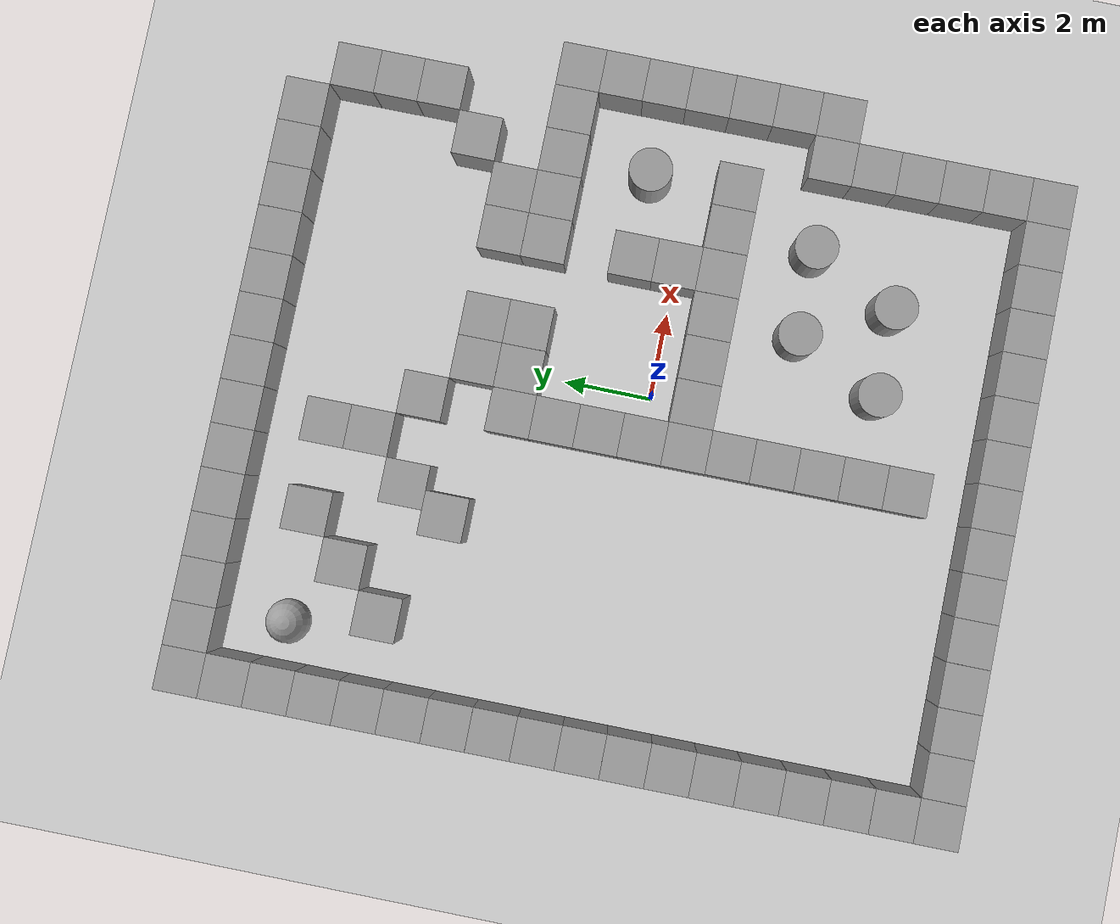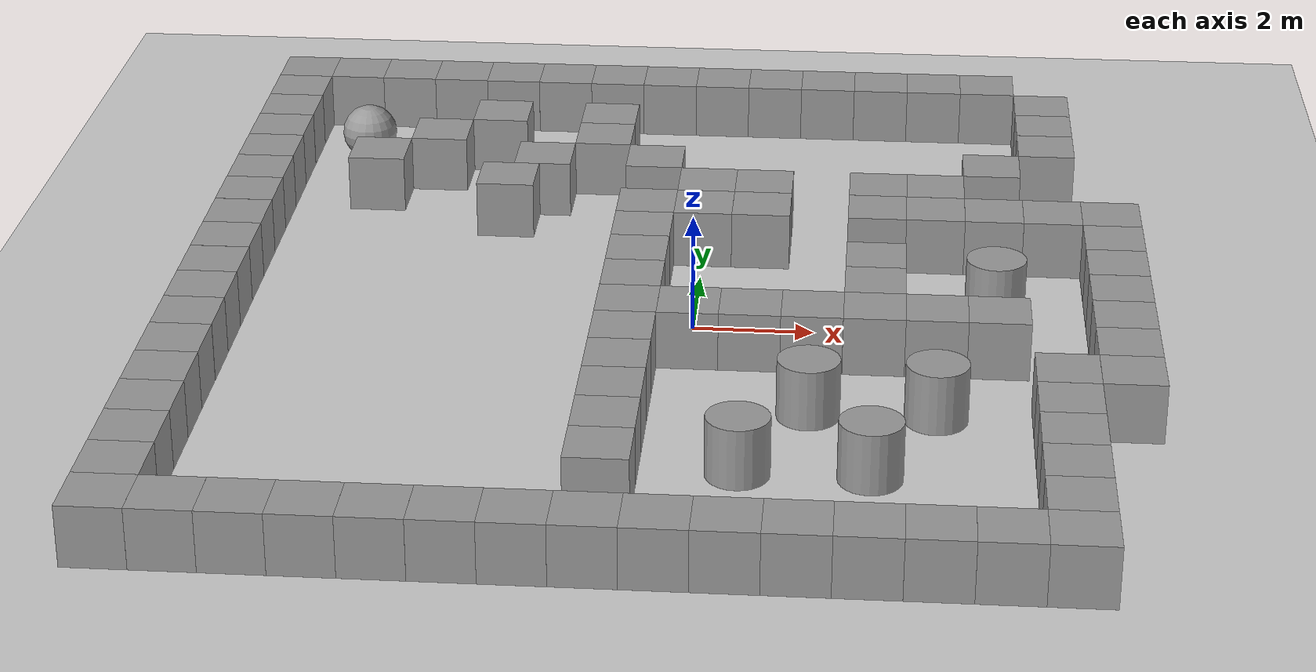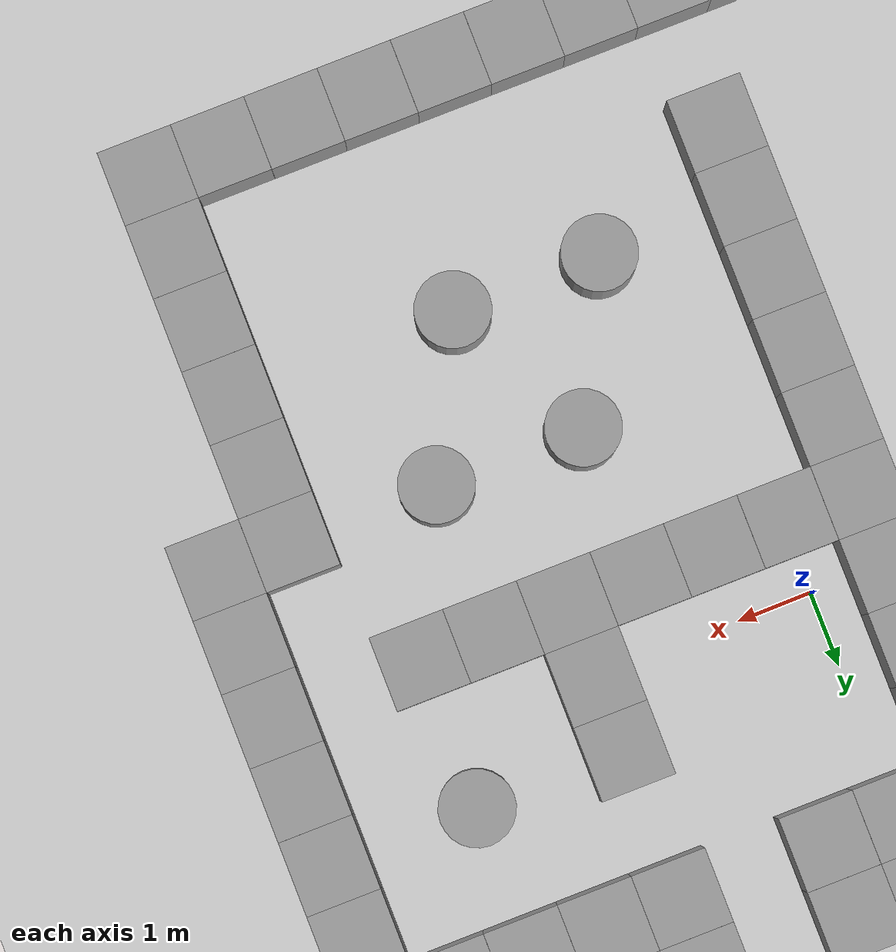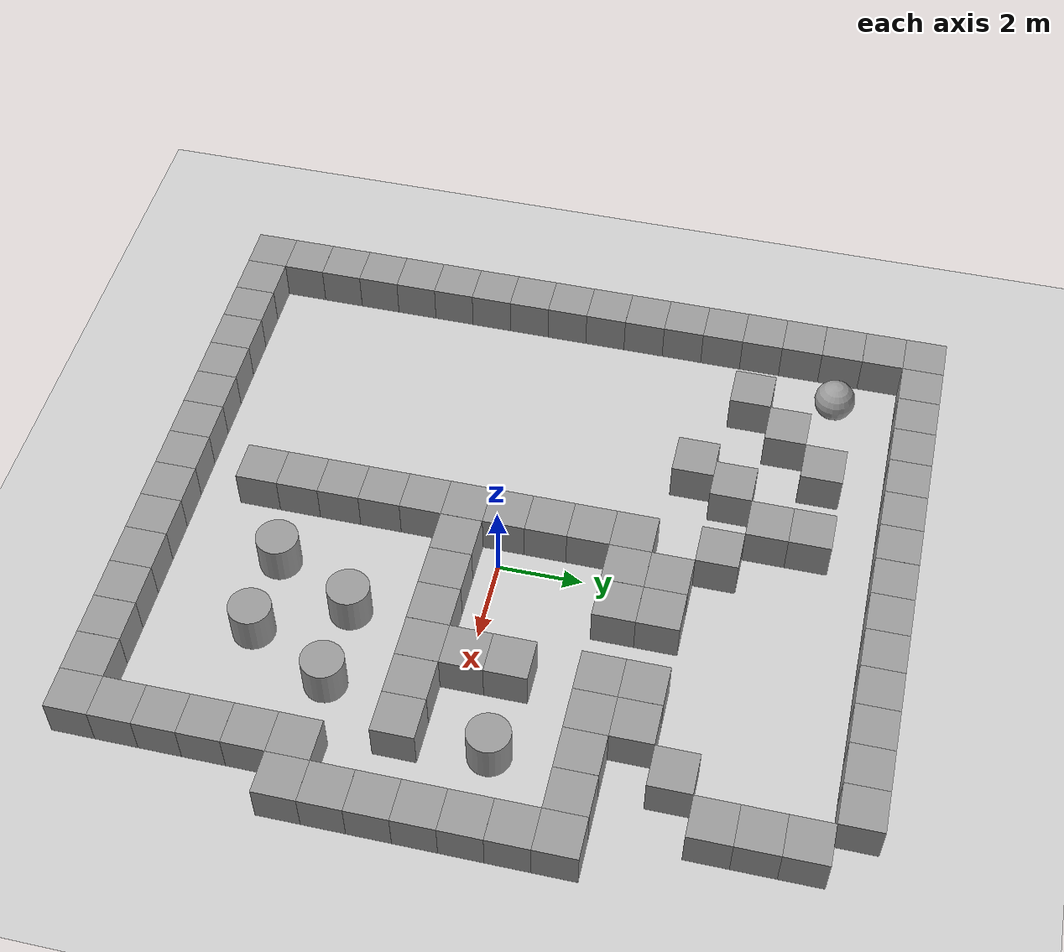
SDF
<sdf version="1.4">
 <world name="default">
  <light name="sun" type="directional">
   <pose>0 0 10 0 -0 0</pose>
   <diffuse>0.8 0.8 0.8 1</diffuse>
   <specular>0.2 0.2 0.2 1</specular>
   <attenuation>
    <range>1000</range>
    <constant>0.9</constant>
    <linear>0.01</linear>
    <quadratic>0.001</quadratic>
   </attenuation>
   <direction>-0.5 0.1 -0.9</direction>
  </light>
  <model name="ground_plane">
   <static>1</static>
   <link name="link">
    <collision name="collision">
     <geometry><plane><normal>0 0 1</normal><size>100 100</size></plane></geometry>
     <surface><friction><ode><mu>100</mu><mu2>50</mu2></ode></friction></surface>
    </collision>
    <visual name="visual">
     <cast_shadows>0</cast_shadows>
     <geometry><plane><normal>0 0 1</normal><size>100 100</size></plane></geometry>
     <material>
      <script><uri>file://media/materials/scripts/gazebo.material</uri><name>Gazebo/Grey</name></script>
     </material>
    </visual>
    <velocity_decay><linear>0</linear><angular>0</angular></velocity_decay>
   </link>
  </model>
  <physics type="ode">
   <max_step_size>0.01</max_step_size>
   <real_time_factor>1</real_time_factor>
   <real_time_update_rate>100</real_time_update_rate>
   <gravity>0 0 -9.8</gravity>
  </physics>
  <scene><ambient>0.4 0.4 0.4 1</ambient><background>0.7 0.7 0.7 1</background><shadows>1</shadows></scene>
  <model name="unit_box_1">
   <pose>5e-06 -0.999881 0.5 0 0 -3.1e-05</pose>
   <link name="link">
    <inertial>
     <mass>1</mass>
     <inertia><ixx>1</ixx><ixy>0</ixy><ixz>0</ixz><iyy>1</iyy><iyz>0</iyz><izz>1</izz></inertia>
    </inertial>
    <collision name="collision"><geometry><box><size>1 1 1</size></box></geometry></collision>
    <visual name="visual">
     <geometry><box><size>1 1 1</size></box></geometry>
     <material>
      <script><uri>file://media/materials/scripts/gazebo.material</uri><name>Gazebo/Grey</name></script>
     </material>
    </visual>
    <velocity_decay><linear>0</linear><angular>0</angular></velocity_decay>
   </link>
   <static>0</static>
  </model>
  <model name="unit_box_2">
   <pose>1.00013 -1.00033 0.5 0 -0 3.1e-05</pose>
   <link name="link">
    <inertial>
     <mass>1</mass>
     <inertia><ixx>1</ixx><ixy>0</ixy><ixz>0</ixz><iyy>1</iyy><iyz>0</iyz><izz>1</izz></inertia>
    </inertial>
    <collision name="collision"><geometry><box><size>1 1 1</size></box></geometry></collision>
    <visual name="visual">
     <geometry><box><size>1 1 1</size></box></geometry>
     <material>
      <script><uri>file://media/materials/scripts/gazebo.material</uri><name>Gazebo/Grey</name></script>
     </material>
    </visual>
    <velocity_decay><linear>0</linear><angular>0</angular></velocity_decay>
   </link>
   <static>0</static>
  </model>
  <model name="unit_box_3">
   <pose>2.00013 -0.999965 0.5 0 -0 2.2e-05</pose>
   <link name="link">
    <inertial>
     <mass>1</mass>
     <inertia><ixx>1</ixx><ixy>0</ixy><ixz>0</ixz><iyy>1</iyy><iyz>0</iyz><izz>1</izz></inertia>
    </inertial>
    <collision name="collision"><geometry><box><size>1 1 1</size></box></geometry></collision>
    <visual name="visual">
     <geometry><box><size>1 1 1</size></box></geometry>
     <material>
      <script><uri>file://media/materials/scripts/gazebo.material</uri><name>Gazebo/Grey</name></script>
     </material>
    </visual>
    <velocity_decay><linear>0</linear><angular>0</angular></velocity_decay>
   </link>
   <static>0</static>
  </model>
  <model name="unit_box_4">
   <pose>3.00033 -1.00003 0.5 0 -0 0.000257</pose>
   <link name="link">
    <inertial>
     <mass>1</mass>
     <inertia><ixx>1</ixx><ixy>0</ixy><ixz>0</ixz><iyy>1</iyy><iyz>0</iyz><izz>1</izz></inertia>
    </inertial>
    <collision name="collision"><geometry><box><size>1 1 1</size></box></geometry></collision>
    <visual name="visual">
     <geometry><box><size>1 1 1</size></box></geometry>
     <material>
      <script><uri>file://media/materials/scripts/gazebo.material</uri><name>Gazebo/Grey</name></script>
     </material>
    </visual>
    <velocity_decay><linear>0</linear><angular>0</angular></velocity_decay>
   </link>
   <static>0</static>
  </model>
  <model name="unit_box_5">
   <pose>3.00021 6.2e-05 0.5 0 -0 0.000131</pose>
   <link name="link">
    <inertial>
     <mass>1</mass>
     <inertia><ixx>1</ixx><ixy>0</ixy><ixz>0</ixz><iyy>1</iyy><iyz>0</iyz><izz>1</izz></inertia>
    </inertial>
    <collision name="collision"><geometry><box><size>1 1 1</size></box></geometry></collision>
    <visual name="visual">
     <geometry><box><size>1 1 1</size></box></geometry>
     <material>
      <script><uri>file://media/materials/scripts/gazebo.material</uri><name>Gazebo/Grey</name></script>
     </material>
    </visual>
    <velocity_decay><linear>0</linear><angular>0</angular></velocity_decay>
   </link>
   <static>0</static>
  </model>
  <model name="unit_box_6">
   <pose>3.00003 1.00015 0.5 -0 -0 -5e-06</pose>
   <link name="link">
    <inertial>
     <mass>1</mass>
     <inertia><ixx>1</ixx><ixy>0</ixy><ixz>0</ixz><iyy>1</iyy><iyz>0</iyz><izz>1</izz></inertia>
    </inertial>
    <collision name="collision"><geometry><box><size>1 1 1</size></box></geometry></collision>
    <visual name="visual">
     <geometry><box><size>1 1 1</size></box></geometry>
     <material>
      <script><uri>file://media/materials/scripts/gazebo.material</uri><name>Gazebo/Grey</name></script>
     </material>
    </visual>
    <velocity_decay><linear>0</linear><angular>0</angular></velocity_decay>
   </link>
   <static>0</static>
  </model>
  <model name="unit_box_7">
   <pose>2.9998 2.99992 0.5 0 -0 -0.000142</pose>
   <link name="link">
    <inertial>
     <mass>1</mass>
     <inertia><ixx>1</ixx><ixy>0</ixy><ixz>0</ixz><iyy>1</iyy><iyz>0</iyz><izz>1</izz></inertia>
    </inertial>
    <collision name="collision"><geometry><box><size>1 1 1</size></box></geometry></collision>
    <visual name="visual">
     <geometry><box><size>1 1 1</size></box></geometry>
     <material>
      <script><uri>file://media/materials/scripts/gazebo.material</uri><name>Gazebo/Grey</name></script>
     </material>
    </visual>
    <velocity_decay><linear>0</linear><angular>0</angular></velocity_decay>
   </link>
   <static>0</static>
  </model>
  <model name="unit_box_8">
   <pose>3.99988 3.00001 0.5 0 0 -0.000169</pose>
   <link name="link">
    <inertial>
     <mass>1</mass>
     <inertia><ixx>1</ixx><ixy>0</ixy><ixz>0</ixz><iyy>1</iyy><iyz>0</iyz><izz>1</izz></inertia>
    </inertial>
    <collision name="collision"><geometry><box><size>1 1 1</size></box></geometry></collision>
    <visual name="visual">
     <geometry><box><size>1 1 1</size></box></geometry>
     <material>
      <script><uri>file://media/materials/scripts/gazebo.material</uri><name>Gazebo/Grey</name></script>
     </material>
    </visual>
    <velocity_decay><linear>0</linear><angular>0</angular></velocity_decay>
   </link>
   <static>0</static>
  </model>
  <model name="unit_box_9">
   <pose>4.99997 3.00003 0.5 0 0 -0.000221</pose>
   <link name="link">
    <inertial>
     <mass>1</mass>
     <inertia><ixx>1</ixx><ixy>0</ixy><ixz>0</ixz><iyy>1</iyy><iyz>0</iyz><izz>1</izz></inertia>
    </inertial>
    <collision name="collision"><geometry><box><size>1 1 1</size></box></geometry></collision>
    <visual name="visual">
     <geometry><box><size>1 1 1</size></box></geometry>
     <material>
      <script><uri>file://media/materials/scripts/gazebo.material</uri><name>Gazebo/Grey</name></script>
     </material>
    </visual>
    <velocity_decay><linear>0</linear><angular>0</angular></velocity_decay>
   </link>
   <static>0</static>
  </model>
  <model name="unit_box_10">
   <pose>6.0002 2.99992 0.5 0 0 -0.000145</pose>
   <link name="link">
    <inertial>
     <mass>1</mass>
     <inertia><ixx>1</ixx><ixy>0</ixy><ixz>0</ixz><iyy>1</iyy><iyz>0</iyz><izz>1</izz></inertia>
    </inertial>
    <collision name="collision"><geometry><box><size>1 1 1</size></box></geometry></collision>
    <visual name="visual">
     <geometry><box><size>1 1 1</size></box></geometry>
     <material>
      <script><uri>file://media/materials/scripts/gazebo.material</uri><name>Gazebo/Grey</name></script>
     </material>
    </visual>
    <velocity_decay><linear>0</linear><angular>0</angular></velocity_decay>
   </link>
   <static>0</static>
  </model>
  <model name="unit_box_11">
   <pose>7.00028 3.00032 0.5 -0 -0 -2.6e-05</pose>
   <link name="link">
    <inertial>
     <mass>1</mass>
     <inertia><ixx>1</ixx><ixy>0</ixy><ixz>0</ixz><iyy>1</iyy><iyz>0</iyz><izz>1</izz></inertia>
    </inertial>
    <collision name="collision"><geometry><box><size>1 1 1</size></box></geometry></collision>
    <visual name="visual">
     <geometry><box><size>1 1 1</size></box></geometry>
     <material>
      <script><uri>file://media/materials/scripts/gazebo.material</uri><name>Gazebo/Grey</name></script>
     </material>
    </visual>
    <velocity_decay><linear>0</linear><angular>0</angular></velocity_decay>
   </link>
   <static>0</static>
  </model>
  <model name="unit_box_12">
   <pose>7.00019 2.00029 0.5 -0 -0 -7.1e-05</pose>
   <link name="link">
    <inertial>
     <mass>1</mass>
     <inertia><ixx>1</ixx><ixy>0</ixy><ixz>0</ixz><iyy>1</iyy><iyz>0</iyz><izz>1</izz></inertia>
    </inertial>
    <collision name="collision"><geometry><box><size>1 1 1</size></box></geometry></collision>
    <visual name="visual">
     <geometry><box><size>1 1 1</size></box></geometry>
     <material>
      <script><uri>file://media/materials/scripts/gazebo.material</uri><name>Gazebo/Grey</name></script>
     </material>
    </visual>
    <velocity_decay><linear>0</linear><angular>0</angular></velocity_decay>
   </link>
   <static>0</static>
  </model>
  <model name="unit_box_13">
   <pose>6.99999 1.00029 0.5 0 -0 -7.1e-05</pose>
   <link name="link">
    <inertial>
     <mass>1</mass>
     <inertia><ixx>1</ixx><ixy>0</ixy><ixz>0</ixz><iyy>1</iyy><iyz>0</iyz><izz>1</izz></inertia>
    </inertial>
    <collision name="collision"><geometry><box><size>1 1 1</size></box></geometry></collision>
    <visual name="visual">
     <geometry><box><size>1 1 1</size></box></geometry>
     <material>
      <script><uri>file://media/materials/scripts/gazebo.material</uri><name>Gazebo/Grey</name></script>
     </material>
    </visual>
    <velocity_decay><linear>0</linear><angular>0</angular></velocity_decay>
   </link>
   <static>0</static>
  </model>
  <model name="unit_box_14">
   <pose>7.00006 0.000151 0.5 0 -0 1e-06</pose>
   <link name="link">
    <inertial>
     <mass>1</mass>
     <inertia><ixx>1</ixx><ixy>0</ixy><ixz>0</ixz><iyy>1</iyy><iyz>0</iyz><izz>1</izz></inertia>
    </inertial>
    <collision name="collision"><geometry><box><size>1 1 1</size></box></geometry></collision>
    <visual name="visual">
     <geometry><box><size>1 1 1</size></box></geometry>
     <material>
      <script><uri>file://media/materials/scripts/gazebo.material</uri><name>Gazebo/Grey</name></script>
     </material>
    </visual>
    <velocity_decay><linear>0</linear><angular>0</angular></velocity_decay>
   </link>
   <static>0</static>
  </model>
  <model name="unit_cylinder_1">
   <pose>5 1 0.49912 -0 -0 -0</pose>
   <link name="link">
    <inertial>
     <mass>1</mass>
     <inertia><ixx>1</ixx><ixy>0</ixy><ixz>0</ixz><iyy>1</iyy><iyz>0</iyz><izz>1</izz></inertia>
    </inertial>
    <collision name="collision">
     <geometry><cylinder><radius>0.5</radius><length>1</length></cylinder></geometry>
    </collision>
    <visual name="visual">
     <geometry><cylinder><radius>0.5</radius><length>1</length></cylinder></geometry>
     <material>
      <script><uri>file://media/materials/scripts/gazebo.material</uri><name>Gazebo/Grey</name></script>
     </material>
    </visual>
    <velocity_decay><linear>0</linear><angular>0</angular></velocity_decay>
   </link>
   <static>0</static>
  </model>
  <model name="unit_box_15">
   <pose>4.00045 -0.999873 0.5 0 -0 6e-06</pose>
   <link name="link">
    <inertial>
     <mass>1</mass>
     <inertia><ixx>1</ixx><ixy>0</ixy><ixz>0</ixz><iyy>1</iyy><iyz>0</iyz><izz>1</izz></inertia>
    </inertial>
    <collision name="collision"><geometry><box><size>1 1 1</size></box></geometry></collision>
    <visual name="visual">
     <geometry><box><size>1 1 1</size></box></geometry>
     <material>
      <script><uri>file://media/materials/scripts/gazebo.material</uri><name>Gazebo/Grey</name></script>
     </material>
    </visual>
    <velocity_decay><linear>0</linear><angular>0</angular></velocity_decay>
   </link>
   <static>0</static>
  </model>
  <model name="unit_box_16">
   <pose>5.00046 -1.00003 0.5 0 -0 1.5e-05</pose>
   <link name="link">
    <inertial>
     <mass>1</mass>
     <inertia><ixx>1</ixx><ixy>0</ixy><ixz>0</ixz><iyy>1</iyy><iyz>0</iyz><izz>1</izz></inertia>
    </inertial>
    <collision name="collision"><geometry><box><size>1 1 1</size></box></geometry></collision>
    <visual name="visual">
     <geometry><box><size>1 1 1</size></box></geometry>
     <material>
      <script><uri>file://media/materials/scripts/gazebo.material</uri><name>Gazebo/Grey</name></script>
     </material>
    </visual>
    <velocity_decay><linear>0</linear><angular>0</angular></velocity_decay>
   </link>
   <static>0</static>
  </model>
  <model name="unit_box_17">
   <pose>7.00035 -0.999923 0.5 0 -0 9.8e-05</pose>
   <link name="link">
    <inertial>
     <mass>1</mass>
     <inertia><ixx>1</ixx><ixy>0</ixy><ixz>0</ixz><iyy>1</iyy><iyz>0</iyz><izz>1</izz></inertia>
    </inertial>
    <collision name="collision"><geometry><box><size>1 1 1</size></box></geometry></collision>
    <visual name="visual">
     <geometry><box><size>1 1 1</size></box></geometry>
     <material>
      <script><uri>file://media/materials/scripts/gazebo.material</uri><name>Gazebo/Grey</name></script>
     </material>
    </visual>
    <velocity_decay><linear>0</linear><angular>0</angular></velocity_decay>
   </link>
   <static>0</static>
  </model>
  <model name="unit_box_18">
   <pose>1.0003 2.99997 0.5 0 -0 6.4e-05</pose>
   <link name="link">
    <inertial>
     <mass>1</mass>
     <inertia><ixx>1</ixx><ixy>0</ixy><ixz>0</ixz><iyy>1</iyy><iyz>0</iyz><izz>1</izz></inertia>
    </inertial>
    <collision name="collision"><geometry><box><size>1 1 1</size></box></geometry></collision>
    <visual name="visual">
     <geometry><box><size>1 1 1</size></box></geometry>
     <material>
      <script><uri>file://media/materials/scripts/gazebo.material</uri><name>Gazebo/Grey</name></script>
     </material>
    </visual>
    <velocity_decay><linear>0</linear><angular>0</angular></velocity_decay>
   </link>
   <static>0</static>
  </model>
  <model name="unit_box_19">
   <pose>9.3e-05 2.99979 0.5 0 -0 0.000304</pose>
   <link name="link">
    <inertial>
     <mass>1</mass>
     <inertia><ixx>1</ixx><ixy>0</ixy><ixz>0</ixz><iyy>1</iyy><iyz>0</iyz><izz>1</izz></inertia>
    </inertial>
    <collision name="collision"><geometry><box><size>1 1 1</size></box></geometry></collision>
    <visual name="visual">
     <geometry><box><size>1 1 1</size></box></geometry>
     <material>
      <script><uri>file://media/materials/scripts/gazebo.material</uri><name>Gazebo/Grey</name></script>
     </material>
    </visual>
    <velocity_decay><linear>0</linear><angular>0</angular></velocity_decay>
   </link>
   <static>0</static>
  </model>
  <model name="unit_box_20">
   <pose>-1.00013 3.00036 0.5 0 0 -3.9e-05</pose>
   <link name="link">
    <inertial>
     <mass>1</mass>
     <inertia><ixx>1</ixx><ixy>0</ixy><ixz>0</ixz><iyy>1</iyy><iyz>0</iyz><izz>1</izz></inertia>
    </inertial>
    <collision name="collision"><geometry><box><size>1 1 1</size></box></geometry></collision>
    <visual name="visual">
     <geometry><box><size>1 1 1</size></box></geometry>
     <material>
      <script><uri>file://media/materials/scripts/gazebo.material</uri><name>Gazebo/Grey</name></script>
     </material>
    </visual>
    <velocity_decay><linear>0</linear><angular>0</angular></velocity_decay>
   </link>
   <static>0</static>
  </model>
  <model name="unit_box_21">
   <pose>-0.999873 2.00036 0.5 -0 -0 -3.9e-05</pose>
   <link name="link">
    <inertial>
     <mass>1</mass>
     <inertia><ixx>1</ixx><ixy>0</ixy><ixz>0</ixz><iyy>1</iyy><iyz>0</iyz><izz>1</izz></inertia>
    </inertial>
    <collision name="collision"><geometry><box><size>1 1 1</size></box></geometry></collision>
    <visual name="visual">
     <geometry><box><size>1 1 1</size></box></geometry>
     <material>
      <script><uri>file://media/materials/scripts/gazebo.material</uri><name>Gazebo/Grey</name></script>
     </material>
    </visual>
    <velocity_decay><linear>0</linear><angular>0</angular></velocity_decay>
   </link>
   <static>0</static>
  </model>
  <model name="unit_box_22">
   <pose>-1.0002 1.00011 0.5 0 0 -4.9e-05</pose>
   <link name="link">
    <inertial>
     <mass>1</mass>
     <inertia><ixx>1</ixx><ixy>0</ixy><ixz>0</ixz><iyy>1</iyy><iyz>0</iyz><izz>1</izz></inertia>
    </inertial>
    <collision name="collision"><geometry><box><size>1 1 1</size></box></geometry></collision>
    <visual name="visual">
     <geometry><box><size>1 1 1</size></box></geometry>
     <material>
      <script><uri>file://media/materials/scripts/gazebo.material</uri><name>Gazebo/Grey</name></script>
     </material>
    </visual>
    <velocity_decay><linear>0</linear><angular>0</angular></velocity_decay>
   </link>
   <static>0</static>
  </model>
  <model name="unit_box_23">
   <pose>-1.00047 9.5e-05 0.5 0 -0 -4.2e-05</pose>
   <link name="link">
    <inertial>
     <mass>1</mass>
     <inertia><ixx>1</ixx><ixy>0</ixy><ixz>0</ixz><iyy>1</iyy><iyz>0</iyz><izz>1</izz></inertia>
    </inertial>
    <collision name="collision"><geometry><box><size>1 1 1</size></box></geometry></collision>
    <visual name="visual">
     <geometry><box><size>1 1 1</size></box></geometry>
     <material>
      <script><uri>file://media/materials/scripts/gazebo.material</uri><name>Gazebo/Grey</name></script>
     </material>
    </visual>
    <velocity_decay><linear>0</linear><angular>0</angular></velocity_decay>
   </link>
   <static>0</static>
  </model>
  <model name="unit_box_24">
   <pose>-1.00037 -0.999916 0.5 -0 -0 -4.6e-05</pose>
   <link name="link">
    <inertial>
     <mass>1</mass>
     <inertia><ixx>1</ixx><ixy>0</ixy><ixz>0</ixz><iyy>1</iyy><iyz>0</iyz><izz>1</izz></inertia>
    </inertial>
    <collision name="collision"><geometry><box><size>1 1 1</size></box></geometry></collision>
    <visual name="visual">
     <geometry><box><size>1 1 1</size></box></geometry>
     <material>
      <script><uri>file://media/materials/scripts/gazebo.material</uri><name>Gazebo/Grey</name></script>
     </material>
    </visual>
    <velocity_decay><linear>0</linear><angular>0</angular></velocity_decay>
   </link>
   <static>0</static>
  </model>
  <model name="unit_box_25">
   <pose>3.0001 4.00019 0.5 -0 -0 -0.000128</pose>
   <link name="link">
    <inertial>
     <mass>1</mass>
     <inertia><ixx>1</ixx><ixy>0</ixy><ixz>0</ixz><iyy>1</iyy><iyz>0</iyz><izz>1</izz></inertia>
    </inertial>
    <collision name="collision"><geometry><box><size>1 1 1</size></box></geometry></collision>
    <visual name="visual">
     <geometry><box><size>1 1 1</size></box></geometry>
     <material>
      <script><uri>file://media/materials/scripts/gazebo.material</uri><name>Gazebo/Grey</name></script>
     </material>
    </visual>
    <velocity_decay><linear>0</linear><angular>0</angular></velocity_decay>
   </link>
   <static>0</static>
  </model>
  <model name="unit_box_26">
   <pose>1.0001 4.00007 0.5 0 0 -4e-06</pose>
   <link name="link">
    <inertial>
     <mass>1</mass>
     <inertia><ixx>1</ixx><ixy>0</ixy><ixz>0</ixz><iyy>1</iyy><iyz>0</iyz><izz>1</izz></inertia>
    </inertial>
    <collision name="collision"><geometry><box><size>1 1 1</size></box></geometry></collision>
    <visual name="visual">
     <geometry><box><size>1 1 1</size></box></geometry>
     <material>
      <script><uri>file://media/materials/scripts/gazebo.material</uri><name>Gazebo/Grey</name></script>
     </material>
    </visual>
    <velocity_decay><linear>0</linear><angular>0</angular></velocity_decay>
   </link>
   <static>0</static>
  </model>
  <model name="unit_box_27">
   <pose>9e-05 3.99999 0.5 0 0 -1.8e-05</pose>
   <link name="link">
    <inertial>
     <mass>1</mass>
     <inertia><ixx>1</ixx><ixy>0</ixy><ixz>0</ixz><iyy>1</iyy><iyz>0</iyz><izz>1</izz></inertia>
    </inertial>
    <collision name="collision"><geometry><box><size>1 1 1</size></box></geometry></collision>
    <visual name="visual">
     <geometry><box><size>1 1 1</size></box></geometry>
     <material>
      <script><uri>file://media/materials/scripts/gazebo.material</uri><name>Gazebo/Grey</name></script>
     </material>
    </visual>
    <velocity_decay><linear>0</linear><angular>0</angular></velocity_decay>
   </link>
   <static>0</static>
  </model>
  <model name="unit_box_28">
   <pose>4.00013 4.00021 0.5 0 -0 -0.000179</pose>
   <link name="link">
    <inertial>
     <mass>1</mass>
     <inertia><ixx>1</ixx><ixy>0</ixy><ixz>0</ixz><iyy>1</iyy><iyz>0</iyz><izz>1</izz></inertia>
    </inertial>
    <collision name="collision"><geometry><box><size>1 1 1</size></box></geometry></collision>
    <visual name="visual">
     <geometry><box><size>1 1 1</size></box></geometry>
     <material>
      <script><uri>file://media/materials/scripts/gazebo.material</uri><name>Gazebo/Grey</name></script>
     </material>
    </visual>
    <velocity_decay><linear>0</linear><angular>0</angular></velocity_decay>
   </link>
   <static>0</static>
  </model>
  <model name="unit_box_29">
   <pose>-0.999949 5 0.5 -0 -0 -4.5e-05</pose>
   <link name="link">
    <inertial>
     <mass>1</mass>
     <inertia><ixx>1</ixx><ixy>0</ixy><ixz>0</ixz><iyy>1</iyy><iyz>0</iyz><izz>1</izz></inertia>
    </inertial>
    <collision name="collision"><geometry><box><size>1 1 1</size></box></geometry></collision>
    <visual name="visual">
     <geometry><box><size>1 1 1</size></box></geometry>
     <material>
      <script><uri>file://media/materials/scripts/gazebo.material</uri><name>Gazebo/Grey</name></script>
     </material>
    </visual>
    <velocity_decay><linear>0</linear><angular>0</angular></velocity_decay>
   </link>
   <static>0</static>
  </model>
  <model name="unit_box_30">
   <pose>-1.99991 5.99986 0.5 0 -0 -7.7e-05</pose>
   <link name="link">
    <inertial>
     <mass>1</mass>
     <inertia><ixx>1</ixx><ixy>0</ixy><ixz>0</ixz><iyy>1</iyy><iyz>0</iyz><izz>1</izz></inertia>
    </inertial>
    <collision name="collision"><geometry><box><size>1 1 1</size></box></geometry></collision>
    <visual name="visual">
     <geometry><box><size>1 1 1</size></box></geometry>
     <material>
      <script><uri>file://media/materials/scripts/gazebo.material</uri><name>Gazebo/Grey</name></script>
     </material>
    </visual>
    <velocity_decay><linear>0</linear><angular>0</angular></velocity_decay>
   </link>
   <static>0</static>
  </model>
  <model name="unit_box_31">
   <pose>4.9999 5.00006 0.5 -0 -0 -0.000173</pose>
   <link name="link">
    <inertial>
     <mass>1</mass>
     <inertia><ixx>1</ixx><ixy>0</ixy><ixz>0</ixz><iyy>1</iyy><iyz>0</iyz><izz>1</izz></inertia>
    </inertial>
    <collision name="collision"><geometry><box><size>1 1 1</size></box></geometry></collision>
    <visual name="visual">
     <geometry><box><size>1 1 1</size></box></geometry>
     <material>
      <script><uri>file://media/materials/scripts/gazebo.material</uri><name>Gazebo/Grey</name></script>
     </material>
    </visual>
    <velocity_decay><linear>0</linear><angular>0</angular></velocity_decay>
   </link>
   <static>0</static>
  </model>
  <model name="unit_box_32">
   <pose>6.00008 5.99998 0.5 0 -0 -9.2e-05</pose>
   <link name="link">
    <inertial>
     <mass>1</mass>
     <inertia><ixx>1</ixx><ixy>0</ixy><ixz>0</ixz><iyy>1</iyy><iyz>0</iyz><izz>1</izz></inertia>
    </inertial>
    <collision name="collision"><geometry><box><size>1 1 1</size></box></geometry></collision>
    <visual name="visual">
     <geometry><box><size>1 1 1</size></box></geometry>
     <material>
      <script><uri>file://media/materials/scripts/gazebo.material</uri><name>Gazebo/Grey</name></script>
     </material>
    </visual>
    <velocity_decay><linear>0</linear><angular>0</angular></velocity_decay>
   </link>
   <static>0</static>
  </model>
  <model name="unit_box_33">
   <pose>-2.00009 6.9999 0.5 0 0 -8.1e-05</pose>
   <link name="link">
    <inertial>
     <mass>1</mass>
     <inertia><ixx>1</ixx><ixy>0</ixy><ixz>0</ixz><iyy>1</iyy><iyz>0</iyz><izz>1</izz></inertia>
    </inertial>
    <collision name="collision"><geometry><box><size>1 1 1</size></box></geometry></collision>
    <visual name="visual">
     <geometry><box><size>1 1 1</size></box></geometry>
     <material>
      <script><uri>file://media/materials/scripts/gazebo.material</uri><name>Gazebo/Grey</name></script>
     </material>
    </visual>
    <velocity_decay><linear>0</linear><angular>0</angular></velocity_decay>
   </link>
   <static>0</static>
  </model>
  <model name="unit_box_34">
   <pose>6.00004 7.00005 0.5 0 0 -0.000127</pose>
   <link name="link">
    <inertial>
     <mass>1</mass>
     <inertia><ixx>1</ixx><ixy>0</ixy><ixz>0</ixz><iyy>1</iyy><iyz>0</iyz><izz>1</izz></inertia>
    </inertial>
    <collision name="collision"><geometry><box><size>1 1 1</size></box></geometry></collision>
    <visual name="visual">
     <geometry><box><size>1 1 1</size></box></geometry>
     <material>
      <script><uri>file://media/materials/scripts/gazebo.material</uri><name>Gazebo/Grey</name></script>
     </material>
    </visual>
    <velocity_decay><linear>0</linear><angular>0</angular></velocity_decay>
   </link>
   <static>0</static>
  </model>
  <model name="unit_box_35">
   <pose>5.99975 8.00005 0.5 -0 -0 -0.000127</pose>
   <link name="link">
    <inertial>
     <mass>1</mass>
     <inertia><ixx>1</ixx><ixy>0</ixy><ixz>0</ixz><iyy>1</iyy><iyz>0</iyz><izz>1</izz></inertia>
    </inertial>
    <collision name="collision"><geometry><box><size>1 1 1</size></box></geometry></collision>
    <visual name="visual">
     <geometry><box><size>1 1 1</size></box></geometry>
     <material>
      <script><uri>file://media/materials/scripts/gazebo.material</uri><name>Gazebo/Grey</name></script>
     </material>
    </visual>
    <velocity_decay><linear>0</linear><angular>0</angular></velocity_decay>
   </link>
   <static>0</static>
  </model>
  <model name="unit_box_36">
   <pose>5.00047 9.00015 0.5 0 0 -4.7e-05</pose>
   <link name="link">
    <inertial>
     <mass>1</mass>
     <inertia><ixx>1</ixx><ixy>0</ixy><ixz>0</ixz><iyy>1</iyy><iyz>0</iyz><izz>1</izz></inertia>
    </inertial>
    <collision name="collision"><geometry><box><size>1 1 1</size></box></geometry></collision>
    <visual name="visual">
     <geometry><box><size>1 1 1</size></box></geometry>
     <material>
      <script><uri>file://media/materials/scripts/gazebo.material</uri><name>Gazebo/Grey</name></script>
     </material>
    </visual>
    <velocity_decay><linear>0</linear><angular>0</angular></velocity_decay>
   </link>
   <static>0</static>
  </model>
  <model name="unit_box_38">
   <pose>-0.999758 9.00014 0.5 0 -0 0.000102</pose>
   <link name="link">
    <inertial>
     <mass>1</mass>
     <inertia><ixx>1</ixx><ixy>0</ixy><ixz>0</ixz><iyy>1</iyy><iyz>0</iyz><izz>1</izz></inertia>
    </inertial>
    <collision name="collision"><geometry><box><size>1 1 1</size></box></geometry></collision>
    <visual name="visual">
     <geometry><box><size>1 1 1</size></box></geometry>
     <material>
      <script><uri>file://media/materials/scripts/gazebo.material</uri><name>Gazebo/Grey</name></script>
     </material>
    </visual>
    <velocity_decay><linear>0</linear><angular>0</angular></velocity_decay>
   </link>
   <static>0</static>
  </model>
  <model name="unit_box_39">
   <pose>4.00046 8.99947 0.5 0 -0 -3.5e-05</pose>
   <link name="link">
    <inertial>
     <mass>1</mass>
     <inertia><ixx>1</ixx><ixy>0</ixy><ixz>0</ixz><iyy>1</iyy><iyz>0</iyz><izz>1</izz></inertia>
    </inertial>
    <collision name="collision"><geometry><box><size>1 1 1</size></box></geometry></collision>
    <visual name="visual">
     <geometry><box><size>1 1 1</size></box></geometry>
     <material>
      <script><uri>file://media/materials/scripts/gazebo.material</uri><name>Gazebo/Grey</name></script>
     </material>
    </visual>
    <velocity_decay><linear>0</linear><angular>0</angular></velocity_decay>
   </link>
   <static>0</static>
  </model>
  <model name="unit_box_40">
   <pose>3.00045 8.99951 0.5 0 0 -5.6e-05</pose>
   <link name="link">
    <inertial>
     <mass>1</mass>
     <inertia><ixx>1</ixx><ixy>0</ixy><ixz>0</ixz><iyy>1</iyy><iyz>0</iyz><izz>1</izz></inertia>
    </inertial>
    <collision name="collision"><geometry><box><size>1 1 1</size></box></geometry></collision>
    <visual name="visual">
     <geometry><box><size>1 1 1</size></box></geometry>
     <material>
      <script><uri>file://media/materials/scripts/gazebo.material</uri><name>Gazebo/Grey</name></script>
     </material>
    </visual>
    <velocity_decay><linear>0</linear><angular>0</angular></velocity_decay>
   </link>
   <static>0</static>
  </model>
  <model name="unit_box_41">
   <pose>2.00028 8.9998 0.5 0 -0 3.1e-05</pose>
   <link name="link">
    <inertial>
     <mass>1</mass>
     <inertia><ixx>1</ixx><ixy>0</ixy><ixz>0</ixz><iyy>1</iyy><iyz>0</iyz><izz>1</izz></inertia>
    </inertial>
    <collision name="collision"><geometry><box><size>1 1 1</size></box></geometry></collision>
    <visual name="visual">
     <geometry><box><size>1 1 1</size></box></geometry>
     <material>
      <script><uri>file://media/materials/scripts/gazebo.material</uri><name>Gazebo/Grey</name></script>
     </material>
    </visual>
    <velocity_decay><linear>0</linear><angular>0</angular></velocity_decay>
   </link>
   <static>0</static>
  </model>
  <model name="unit_box_42">
   <pose>0.000249 8.99966 0.5 0 -0 9.7e-05</pose>
   <link name="link">
    <inertial>
     <mass>1</mass>
     <inertia><ixx>1</ixx><ixy>0</ixy><ixz>0</ixz><iyy>1</iyy><iyz>0</iyz><izz>1</izz></inertia>
    </inertial>
    <collision name="collision"><geometry><box><size>1 1 1</size></box></geometry></collision>
    <visual name="visual">
     <geometry><box><size>1 1 1</size></box></geometry>
     <material>
      <script><uri>file://media/materials/scripts/gazebo.material</uri><name>Gazebo/Grey</name></script>
     </material>
    </visual>
    <velocity_decay><linear>0</linear><angular>0</angular></velocity_decay>
   </link>
   <static>0</static>
  </model>
  <model name="unit_box_43">
   <pose>1.00025 8.99995 0.5 0 -0 9.7e-05</pose>
   <link name="link">
    <inertial>
     <mass>1</mass>
     <inertia><ixx>1</ixx><ixy>0</ixy><ixz>0</ixz><iyy>1</iyy><iyz>0</iyz><izz>1</izz></inertia>
    </inertial>
    <collision name="collision"><geometry><box><size>1 1 1</size></box></geometry></collision>
    <visual name="visual">
     <geometry><box><size>1 1 1</size></box></geometry>
     <material>
      <script><uri>file://media/materials/scripts/gazebo.material</uri><name>Gazebo/Grey</name></script>
     </material>
    </visual>
    <velocity_decay><linear>0</linear><angular>0</angular></velocity_decay>
   </link>
   <static>0</static>
  </model>
  <model name="unit_box_44">
   <pose>6.99986 -1.99996 0.5 0 -0 0.000172</pose>
   <link name="link">
    <inertial>
     <mass>1</mass>
     <inertia><ixx>1</ixx><ixy>0</ixy><ixz>0</ixz><iyy>1</iyy><iyz>0</iyz><izz>1</izz></inertia>
    </inertial>
    <collision name="collision"><geometry><box><size>1 1 1</size></box></geometry></collision>
    <visual name="visual">
     <geometry><box><size>1 1 1</size></box></geometry>
     <material>
      <script><uri>file://media/materials/scripts/gazebo.material</uri><name>Gazebo/Grey</name></script>
     </material>
    </visual>
    <velocity_decay><linear>0</linear><angular>0</angular></velocity_decay>
   </link>
   <static>0</static>
  </model>
  <model name="unit_box_45">
   <pose>7.00008 -3.00005 0.5 0 -0 8e-05</pose>
   <link name="link">
    <inertial>
     <mass>1</mass>
     <inertia><ixx>1</ixx><ixy>0</ixy><ixz>0</ixz><iyy>1</iyy><iyz>0</iyz><izz>1</izz></inertia>
    </inertial>
    <collision name="collision"><geometry><box><size>1 1 1</size></box></geometry></collision>
    <visual name="visual">
     <geometry><box><size>1 1 1</size></box></geometry>
     <material>
      <script><uri>file://media/materials/scripts/gazebo.material</uri><name>Gazebo/Grey</name></script>
     </material>
    </visual>
    <velocity_decay><linear>0</linear><angular>0</angular></velocity_decay>
   </link>
   <static>0</static>
  </model>
  <model name="unit_box_59">
   <pose>5.99996 -2.99948 0.5 0 -0 8.8e-05</pose>
   <link name="link">
    <inertial>
     <mass>1</mass>
     <inertia><ixx>1</ixx><ixy>0</ixy><ixz>0</ixz><iyy>1</iyy><iyz>0</iyz><izz>1</izz></inertia>
    </inertial>
    <collision name="collision"><geometry><box><size>1 1 1</size></box></geometry></collision>
    <visual name="visual">
     <geometry><box><size>1 1 1</size></box></geometry>
     <material>
      <script><uri>file://media/materials/scripts/gazebo.material</uri><name>Gazebo/Grey</name></script>
     </material>
    </visual>
    <velocity_decay><linear>0</linear><angular>0</angular></velocity_decay>
   </link>
   <static>0</static>
  </model>
  <model name="unit_box_60">
   <pose>5.99974 -3.99959 0.5 -0 -0 -0.000124</pose>
   <link name="link">
    <inertial>
     <mass>1</mass>
     <inertia><ixx>1</ixx><ixy>0</ixy><ixz>0</ixz><iyy>1</iyy><iyz>0</iyz><izz>1</izz></inertia>
    </inertial>
    <collision name="collision"><geometry><box><size>1 1 1</size></box></geometry></collision>
    <visual name="visual">
     <geometry><box><size>1 1 1</size></box></geometry>
     <material>
      <script><uri>file://media/materials/scripts/gazebo.material</uri><name>Gazebo/Grey</name></script>
     </material>
    </visual>
    <velocity_decay><linear>0</linear><angular>0</angular></velocity_decay>
   </link>
   <static>0</static>
  </model>
  <model name="unit_box_61">
   <pose>6.00018 -4.99974 0.5 0 -0 -0.000116</pose>
   <link name="link">
    <inertial>
     <mass>1</mass>
     <inertia><ixx>1</ixx><ixy>0</ixy><ixz>0</ixz><iyy>1</iyy><iyz>0</iyz><izz>1</izz></inertia>
    </inertial>
    <collision name="collision"><geometry><box><size>1 1 1</size></box></geometry></collision>
    <visual name="visual">
     <geometry><box><size>1 1 1</size></box></geometry>
     <material>
      <script><uri>file://media/materials/scripts/gazebo.material</uri><name>Gazebo/Grey</name></script>
     </material>
    </visual>
    <velocity_decay><linear>0</linear><angular>0</angular></velocity_decay>
   </link>
   <static>0</static>
  </model>
  <model name="unit_box_62">
   <pose>6.00048 -5.99991 0.5 0 -0 0.000214</pose>
   <link name="link">
    <inertial>
     <mass>1</mass>
     <inertia><ixx>1</ixx><ixy>0</ixy><ixz>0</ixz><iyy>1</iyy><iyz>0</iyz><izz>1</izz></inertia>
    </inertial>
    <collision name="collision"><geometry><box><size>1 1 1</size></box></geometry></collision>
    <visual name="visual">
     <geometry><box><size>1 1 1</size></box></geometry>
     <material>
      <script><uri>file://media/materials/scripts/gazebo.material</uri><name>Gazebo/Grey</name></script>
     </material>
    </visual>
    <velocity_decay><linear>0</linear><angular>0</angular></velocity_decay>
   </link>
   <static>0</static>
  </model>
  <model name="unit_box_63">
   <pose>6.00055 -7.00006 0.5 0 -0 7e-05</pose>
   <link name="link">
    <inertial>
     <mass>1</mass>
     <inertia><ixx>1</ixx><ixy>0</ixy><ixz>0</ixz><iyy>1</iyy><iyz>0</iyz><izz>1</izz></inertia>
    </inertial>
    <collision name="collision"><geometry><box><size>1 1 1</size></box></geometry></collision>
    <visual name="visual">
     <geometry><box><size>1 1 1</size></box></geometry>
     <material>
      <script><uri>file://media/materials/scripts/gazebo.material</uri><name>Gazebo/Grey</name></script>
     </material>
    </visual>
    <velocity_decay><linear>0</linear><angular>0</angular></velocity_decay>
   </link>
   <static>0</static>
  </model>
  <model name="unit_box_64">
   <pose>6.00063 -8.00016 0.5 0 0 -0.000132</pose>
   <link name="link">
    <inertial>
     <mass>1</mass>
     <inertia><ixx>1</ixx><ixy>0</ixy><ixz>0</ixz><iyy>1</iyy><iyz>0</iyz><izz>1</izz></inertia>
    </inertial>
    <collision name="collision"><geometry><box><size>1 1 1</size></box></geometry></collision>
    <visual name="visual">
     <geometry><box><size>1 1 1</size></box></geometry>
     <material>
      <script><uri>file://media/materials/scripts/gazebo.material</uri><name>Gazebo/Grey</name></script>
     </material>
    </visual>
    <velocity_decay><linear>0</linear><angular>0</angular></velocity_decay>
   </link>
   <static>0</static>
  </model>
  <model name="unit_box_65">
   <pose>5.00063 -8.00035 0.5 0 -0 -0.000132</pose>
   <link name="link">
    <inertial>
     <mass>1</mass>
     <inertia><ixx>1</ixx><ixy>0</ixy><ixz>0</ixz><iyy>1</iyy><iyz>0</iyz><izz>1</izz></inertia>
    </inertial>
    <collision name="collision"><geometry><box><size>1 1 1</size></box></geometry></collision>
    <visual name="visual">
     <geometry><box><size>1 1 1</size></box></geometry>
     <material>
      <script><uri>file://media/materials/scripts/gazebo.material</uri><name>Gazebo/Grey</name></script>
     </material>
    </visual>
    <velocity_decay><linear>0</linear><angular>0</angular></velocity_decay>
   </link>
   <static>0</static>
  </model>
  <model name="unit_box_66">
   <pose>4.00054 -7.99937 0.5 0 -0 1.6e-05</pose>
   <link name="link">
    <inertial>
     <mass>1</mass>
     <inertia><ixx>1</ixx><ixy>0</ixy><ixz>0</ixz><iyy>1</iyy><iyz>0</iyz><izz>1</izz></inertia>
    </inertial>
    <collision name="collision"><geometry><box><size>1 1 1</size></box></geometry></collision>
    <visual name="visual">
     <geometry><box><size>1 1 1</size></box></geometry>
     <material>
      <script><uri>file://media/materials/scripts/gazebo.material</uri><name>Gazebo/Grey</name></script>
     </material>
    </visual>
    <velocity_decay><linear>0</linear><angular>0</angular></velocity_decay>
   </link>
   <static>0</static>
  </model>
  <model name="unit_box_67">
   <pose>-0.999492 -1.99993 0.5 0 0 -7.6e-05</pose>
   <link name="link">
    <inertial>
     <mass>1</mass>
     <inertia><ixx>1</ixx><ixy>0</ixy><ixz>0</ixz><iyy>1</iyy><iyz>0</iyz><izz>1</izz></inertia>
    </inertial>
    <collision name="collision"><geometry><box><size>1 1 1</size></box></geometry></collision>
    <visual name="visual">
     <geometry><box><size>1 1 1</size></box></geometry>
     <material>
      <script><uri>file://media/materials/scripts/gazebo.material</uri><name>Gazebo/Grey</name></script>
     </material>
    </visual>
    <velocity_decay><linear>0</linear><angular>0</angular></velocity_decay>
   </link>
   <static>0</static>
  </model>
  <model name="unit_box_68">
   <pose>-0.9997 -2.99997 0.5 0 -0 -9.4e-05</pose>
   <link name="link">
    <inertial>
     <mass>1</mass>
     <inertia><ixx>1</ixx><ixy>0</ixy><ixz>0</ixz><iyy>1</iyy><iyz>0</iyz><izz>1</izz></inertia>
    </inertial>
    <collision name="collision"><geometry><box><size>1 1 1</size></box></geometry></collision>
    <visual name="visual">
     <geometry><box><size>1 1 1</size></box></geometry>
     <material>
      <script><uri>file://media/materials/scripts/gazebo.material</uri><name>Gazebo/Grey</name></script>
     </material>
    </visual>
    <velocity_decay><linear>0</linear><angular>0</angular></velocity_decay>
   </link>
   <static>0</static>
  </model>
  <model name="unit_box_69">
   <pose>-0.999901 -4.00006 0.5 0 0 -8.7e-05</pose>
   <link name="link">
    <inertial>
     <mass>1</mass>
     <inertia><ixx>1</ixx><ixy>0</ixy><ixz>0</ixz><iyy>1</iyy><iyz>0</iyz><izz>1</izz></inertia>
    </inertial>
    <collision name="collision"><geometry><box><size>1 1 1</size></box></geometry></collision>
    <visual name="visual">
     <geometry><box><size>1 1 1</size></box></geometry>
     <material>
      <script><uri>file://media/materials/scripts/gazebo.material</uri><name>Gazebo/Grey</name></script>
     </material>
    </visual>
    <velocity_decay><linear>0</linear><angular>0</angular></velocity_decay>
   </link>
   <static>0</static>
  </model>
  <model name="unit_box_70">
   <pose>-0.999723 -5.00009 0.5 0 0 -0.000119</pose>
   <link name="link">
    <inertial>
     <mass>1</mass>
     <inertia><ixx>1</ixx><ixy>0</ixy><ixz>0</ixz><iyy>1</iyy><iyz>0</iyz><izz>1</izz></inertia>
    </inertial>
    <collision name="collision"><geometry><box><size>1 1 1</size></box></geometry></collision>
    <visual name="visual">
     <geometry><box><size>1 1 1</size></box></geometry>
     <material>
      <script><uri>file://media/materials/scripts/gazebo.material</uri><name>Gazebo/Grey</name></script>
     </material>
    </visual>
    <velocity_decay><linear>0</linear><angular>0</angular></velocity_decay>
   </link>
   <static>0</static>
  </model>
  <model name="unit_box_71">
   <pose>3.00034 -7.99992 0.5 0 0 -0.000136</pose>
   <link name="link">
    <inertial>
     <mass>1</mass>
     <inertia><ixx>1</ixx><ixy>0</ixy><ixz>0</ixz><iyy>1</iyy><iyz>0</iyz><izz>1</izz></inertia>
    </inertial>
    <collision name="collision"><geometry><box><size>1 1 1</size></box></geometry></collision>
    <visual name="visual">
     <geometry><box><size>1 1 1</size></box></geometry>
     <material>
      <script><uri>file://media/materials/scripts/gazebo.material</uri><name>Gazebo/Grey</name></script>
     </material>
    </visual>
    <velocity_decay><linear>0</linear><angular>0</angular></velocity_decay>
   </link>
   <static>0</static>
  </model>
  <model name="unit_box_72">
   <pose>2.00026 -7.9999 0.5 0 -0 1.6e-05</pose>
   <link name="link">
    <inertial>
     <mass>1</mass>
     <inertia><ixx>1</ixx><ixy>0</ixy><ixz>0</ixz><iyy>1</iyy><iyz>0</iyz><izz>1</izz></inertia>
    </inertial>
    <collision name="collision"><geometry><box><size>1 1 1</size></box></geometry></collision>
    <visual name="visual">
     <geometry><box><size>1 1 1</size></box></geometry>
     <material>
      <script><uri>file://media/materials/scripts/gazebo.material</uri><name>Gazebo/Grey</name></script>
     </material>
    </visual>
    <velocity_decay><linear>0</linear><angular>0</angular></velocity_decay>
   </link>
   <static>0</static>
  </model>
  <model name="unit_box_73">
   <pose>-0.99989 -6.00013 0.5 0 0 -0.000179</pose>
   <link name="link">
    <inertial>
     <mass>1</mass>
     <inertia><ixx>1</ixx><ixy>0</ixy><ixz>0</ixz><iyy>1</iyy><iyz>0</iyz><izz>1</izz></inertia>
    </inertial>
    <collision name="collision"><geometry><box><size>1 1 1</size></box></geometry></collision>
    <visual name="visual">
     <geometry><box><size>1 1 1</size></box></geometry>
     <material>
      <script><uri>file://media/materials/scripts/gazebo.material</uri><name>Gazebo/Grey</name></script>
     </material>
    </visual>
    <velocity_decay><linear>0</linear><angular>0</angular></velocity_decay>
   </link>
   <static>0</static>
  </model>
  <model name="unit_box_74">
   <pose>1.00021 -7.99986 0.5 0 -0 1.7e-05</pose>
   <link name="link">
    <inertial>
     <mass>1</mass>
     <inertia><ixx>1</ixx><ixy>0</ixy><ixz>0</ixz><iyy>1</iyy><iyz>0</iyz><izz>1</izz></inertia>
    </inertial>
    <collision name="collision"><geometry><box><size>1 1 1</size></box></geometry></collision>
    <visual name="visual">
     <geometry><box><size>1 1 1</size></box></geometry>
     <material>
      <script><uri>file://media/materials/scripts/gazebo.material</uri><name>Gazebo/Grey</name></script>
     </material>
    </visual>
    <velocity_decay><linear>0</linear><angular>0</angular></velocity_decay>
   </link>
   <static>0</static>
  </model>
  <model name="unit_box_75">
   <pose>0.000214 -7.99971 0.5 0 -0 1.8e-05</pose>
   <link name="link">
    <inertial>
     <mass>1</mass>
     <inertia><ixx>1</ixx><ixy>0</ixy><ixz>0</ixz><iyy>1</iyy><iyz>0</iyz><izz>1</izz></inertia>
    </inertial>
    <collision name="collision"><geometry><box><size>1 1 1</size></box></geometry></collision>
    <visual name="visual">
     <geometry><box><size>1 1 1</size></box></geometry>
     <material>
      <script><uri>file://media/materials/scripts/gazebo.material</uri><name>Gazebo/Grey</name></script>
     </material>
    </visual>
    <velocity_decay><linear>0</linear><angular>0</angular></velocity_decay>
   </link>
   <static>0</static>
  </model>
  <model name="unit_box_76">
   <pose>-0.999825 -7.99962 0.5 0 -0 1.5e-05</pose>
   <link name="link">
    <inertial>
     <mass>1</mass>
     <inertia><ixx>1</ixx><ixy>0</ixy><ixz>0</ixz><iyy>1</iyy><iyz>0</iyz><izz>1</izz></inertia>
    </inertial>
    <collision name="collision"><geometry><box><size>1 1 1</size></box></geometry></collision>
    <visual name="visual">
     <geometry><box><size>1 1 1</size></box></geometry>
     <material>
      <script><uri>file://media/materials/scripts/gazebo.material</uri><name>Gazebo/Grey</name></script>
     </material>
    </visual>
    <velocity_decay><linear>0</linear><angular>0</angular></velocity_decay>
   </link>
   <static>0</static>
  </model>
  <model name="unit_cylinder_2">
   <pose>4 -3 0.49912 -0 -0 -0</pose>
   <link name="link">
    <inertial>
     <mass>1</mass>
     <inertia><ixx>1</ixx><ixy>0</ixy><ixz>0</ixz><iyy>1</iyy><iyz>0</iyz><izz>1</izz></inertia>
    </inertial>
    <collision name="collision">
     <geometry><cylinder><radius>0.5</radius><length>1</length></cylinder></geometry>
    </collision>
    <visual name="visual">
     <geometry><cylinder><radius>0.5</radius><length>1</length></cylinder></geometry>
     <material>
      <script><uri>file://media/materials/scripts/gazebo.material</uri><name>Gazebo/Grey</name></script>
     </material>
    </visual>
    <velocity_decay><linear>0</linear><angular>0</angular></velocity_decay>
   </link>
   <static>0</static>
  </model>
  <model name="unit_cylinder_3">
   <pose>3 -5 0.49912 -0 -0 -0</pose>
   <link name="link">
    <inertial>
     <mass>1</mass>
     <inertia><ixx>1</ixx><ixy>0</ixy><ixz>0</ixz><iyy>1</iyy><iyz>0</iyz><izz>1</izz></inertia>
    </inertial>
    <collision name="collision">
     <geometry><cylinder><radius>0.5</radius><length>1</length></cylinder></geometry>
    </collision>
    <visual name="visual">
     <geometry><cylinder><radius>0.5</radius><length>1</length></cylinder></geometry>
     <material>
      <script><uri>file://media/materials/scripts/gazebo.material</uri><name>Gazebo/Grey</name></script>
     </material>
    </visual>
    <velocity_decay><linear>0</linear><angular>0</angular></velocity_decay>
   </link>
   <static>0</static>
  </model>
  <model name="unit_cylinder_4">
   <pose>2 -3 0.49912 -0 -0 -0</pose>
   <link name="link">
    <inertial>
     <mass>1</mass>
     <inertia><ixx>1</ixx><ixy>0</ixy><ixz>0</ixz><iyy>1</iyy><iyz>0</iyz><izz>1</izz></inertia>
    </inertial>
    <collision name="collision">
     <geometry><cylinder><radius>0.5</radius><length>1</length></cylinder></geometry>
    </collision>
    <visual name="visual">
     <geometry><cylinder><radius>0.5</radius><length>1</length></cylinder></geometry>
     <material>
      <script><uri>file://media/materials/scripts/gazebo.material</uri><name>Gazebo/Grey</name></script>
     </material>
    </visual>
    <velocity_decay><linear>0</linear><angular>0</angular></velocity_decay>
   </link>
   <static>0</static>
  </model>
  <model name="unit_cylinder_5">
   <pose>1 -5 0.49912 -0 -0 -0</pose>
   <link name="link">
    <inertial>
     <mass>1</mass>
     <inertia><ixx>1</ixx><ixy>0</ixy><ixz>0</ixz><iyy>1</iyy><iyz>0</iyz><izz>1</izz></inertia>
    </inertial>
    <collision name="collision">
     <geometry><cylinder><radius>0.5</radius><length>1</length></cylinder></geometry>
    </collision>
    <visual name="visual">
     <geometry><cylinder><radius>0.5</radius><length>1</length></cylinder></geometry>
     <material>
      <script><uri>file://media/materials/scripts/gazebo.material</uri><name>Gazebo/Grey</name></script>
     </material>
    </visual>
    <velocity_decay><linear>0</linear><angular>0</angular></velocity_decay>
   </link>
   <static>0</static>
  </model>
  <model name="unit_box_77">
   <pose>-1.99992 -8.00007 0.5 0 0 -1.7e-05</pose>
   <link name="link">
    <inertial>
     <mass>1</mass>
     <inertia><ixx>1</ixx><ixy>0</ixy><ixz>0</ixz><iyy>1</iyy><iyz>0</iyz><izz>1</izz></inertia>
    </inertial>
    <collision name="collision"><geometry><box><size>1 1 1</size></box></geometry></collision>
    <visual name="visual">
     <geometry><box><size>1 1 1</size></box></geometry>
     <material>
      <script><uri>file://media/materials/scripts/gazebo.material</uri><name>Gazebo/Grey</name></script>
     </material>
    </visual>
    <velocity_decay><linear>0</linear><angular>0</angular></velocity_decay>
   </link>
   <static>0</static>
  </model>
  <model name="unit_box_78">
   <pose>-2.99992 -7.99999 0.5 0 -0 -1.7e-05</pose>
   <link name="link">
    <inertial>
     <mass>1</mass>
     <inertia><ixx>1</ixx><ixy>0</ixy><ixz>0</ixz><iyy>1</iyy><iyz>0</iyz><izz>1</izz></inertia>
    </inertial>
    <collision name="collision"><geometry><box><size>1 1 1</size></box></geometry></collision>
    <visual name="visual">
     <geometry><box><size>1 1 1</size></box></geometry>
     <material>
      <script><uri>file://media/materials/scripts/gazebo.material</uri><name>Gazebo/Grey</name></script>
     </material>
    </visual>
    <velocity_decay><linear>0</linear><angular>0</angular></velocity_decay>
   </link>
   <static>0</static>
  </model>
  <model name="unit_box_79">
   <pose>-4 -8.00012 0.5 0 -0 -3.9e-05</pose>
   <link name="link">
    <inertial>
     <mass>1</mass>
     <inertia><ixx>1</ixx><ixy>0</ixy><ixz>0</ixz><iyy>1</iyy><iyz>0</iyz><izz>1</izz></inertia>
    </inertial>
    <collision name="collision"><geometry><box><size>1 1 1</size></box></geometry></collision>
    <visual name="visual">
     <geometry><box><size>1 1 1</size></box></geometry>
     <material>
      <script><uri>file://media/materials/scripts/gazebo.material</uri><name>Gazebo/Grey</name></script>
     </material>
    </visual>
    <velocity_decay><linear>0</linear><angular>0</angular></velocity_decay>
   </link>
   <static>0</static>
  </model>
  <model name="unit_box_80">
   <pose>-5.00012 -8.00001 0.5 0 -0 9e-06</pose>
   <link name="link">
    <inertial>
     <mass>1</mass>
     <inertia><ixx>1</ixx><ixy>0</ixy><ixz>0</ixz><iyy>1</iyy><iyz>0</iyz><izz>1</izz></inertia>
    </inertial>
    <collision name="collision"><geometry><box><size>1 1 1</size></box></geometry></collision>
    <visual name="visual">
     <geometry><box><size>1 1 1</size></box></geometry>
     <material>
      <script><uri>file://media/materials/scripts/gazebo.material</uri><name>Gazebo/Grey</name></script>
     </material>
    </visual>
    <velocity_decay><linear>0</linear><angular>0</angular></velocity_decay>
   </link>
   <static>0</static>
  </model>
  <model name="unit_box_81">
   <pose>-6.00023 -7.99987 0.5 0 -0 4.6e-05</pose>
   <link name="link">
    <inertial>
     <mass>1</mass>
     <inertia><ixx>1</ixx><ixy>0</ixy><ixz>0</ixz><iyy>1</iyy><iyz>0</iyz><izz>1</izz></inertia>
    </inertial>
    <collision name="collision"><geometry><box><size>1 1 1</size></box></geometry></collision>
    <visual name="visual">
     <geometry><box><size>1 1 1</size></box></geometry>
     <material>
      <script><uri>file://media/materials/scripts/gazebo.material</uri><name>Gazebo/Grey</name></script>
     </material>
    </visual>
    <velocity_decay><linear>0</linear><angular>0</angular></velocity_decay>
   </link>
   <static>0</static>
  </model>
  <model name="unit_box_82">
   <pose>-7.00074 -7.99971 0.5 0 -0 0.000598</pose>
   <link name="link">
    <inertial>
     <mass>1</mass>
     <inertia><ixx>1</ixx><ixy>0</ixy><ixz>0</ixz><iyy>1</iyy><iyz>0</iyz><izz>1</izz></inertia>
    </inertial>
    <collision name="collision"><geometry><box><size>1 1 1</size></box></geometry></collision>
    <visual name="visual">
     <geometry><box><size>1 1 1</size></box></geometry>
     <material>
      <script><uri>file://media/materials/scripts/gazebo.material</uri><name>Gazebo/Grey</name></script>
     </material>
    </visual>
    <velocity_decay><linear>0</linear><angular>0</angular></velocity_decay>
   </link>
   <static>0</static>
  </model>
  <model name="unit_box_83">
   <pose>-8.00088 -8.00022 0.5 0 -0 0.000403</pose>
   <link name="link">
    <inertial>
     <mass>1</mass>
     <inertia><ixx>1</ixx><ixy>0</ixy><ixz>0</ixz><iyy>1</iyy><iyz>0</iyz><izz>1</izz></inertia>
    </inertial>
    <collision name="collision"><geometry><box><size>1 1 1</size></box></geometry></collision>
    <visual name="visual">
     <geometry><box><size>1 1 1</size></box></geometry>
     <material>
      <script><uri>file://media/materials/scripts/gazebo.material</uri><name>Gazebo/Grey</name></script>
     </material>
    </visual>
    <velocity_decay><linear>0</linear><angular>0</angular></velocity_decay>
   </link>
   <static>0</static>
  </model>
  <model name="unit_box_84">
   <pose>-8.00004 -7.00021 0.5 0 -0 0.000404</pose>
   <link name="link">
    <inertial>
     <mass>1</mass>
     <inertia><ixx>1</ixx><ixy>0</ixy><ixz>0</ixz><iyy>1</iyy><iyz>0</iyz><izz>1</izz></inertia>
    </inertial>
    <collision name="collision"><geometry><box><size>1 1 1</size></box></geometry></collision>
    <visual name="visual">
     <geometry><box><size>1 1 1</size></box></geometry>
     <material>
      <script><uri>file://media/materials/scripts/gazebo.material</uri><name>Gazebo/Grey</name></script>
     </material>
    </visual>
    <velocity_decay><linear>0</linear><angular>0</angular></velocity_decay>
   </link>
   <static>0</static>
  </model>
  <model name="unit_box_85">
   <pose>-7.9996 -6.00007 0.5 0 -0 0.000354</pose>
   <link name="link">
    <inertial>
     <mass>1</mass>
     <inertia><ixx>1</ixx><ixy>0</ixy><ixz>0</ixz><iyy>1</iyy><iyz>0</iyz><izz>1</izz></inertia>
    </inertial>
    <collision name="collision"><geometry><box><size>1 1 1</size></box></geometry></collision>
    <visual name="visual">
     <geometry><box><size>1 1 1</size></box></geometry>
     <material>
      <script><uri>file://media/materials/scripts/gazebo.material</uri><name>Gazebo/Grey</name></script>
     </material>
    </visual>
    <velocity_decay><linear>0</linear><angular>0</angular></velocity_decay>
   </link>
   <static>0</static>
  </model>
  <model name="unit_box_86">
   <pose>-8.00027 -5.00006 0.5 0 -0 0.000332</pose>
   <link name="link">
    <inertial>
     <mass>1</mass>
     <inertia><ixx>1</ixx><ixy>0</ixy><ixz>0</ixz><iyy>1</iyy><iyz>0</iyz><izz>1</izz></inertia>
    </inertial>
    <collision name="collision"><geometry><box><size>1 1 1</size></box></geometry></collision>
    <visual name="visual">
     <geometry><box><size>1 1 1</size></box></geometry>
     <material>
      <script><uri>file://media/materials/scripts/gazebo.material</uri><name>Gazebo/Grey</name></script>
     </material>
    </visual>
    <velocity_decay><linear>0</linear><angular>0</angular></velocity_decay>
   </link>
   <static>0</static>
  </model>
  <model name="unit_box_87">
   <pose>-8.00053 -4.00004 0.5 0 -0 0.000312</pose>
   <link name="link">
    <inertial>
     <mass>1</mass>
     <inertia><ixx>1</ixx><ixy>0</ixy><ixz>0</ixz><iyy>1</iyy><iyz>0</iyz><izz>1</izz></inertia>
    </inertial>
    <collision name="collision"><geometry><box><size>1 1 1</size></box></geometry></collision>
    <visual name="visual">
     <geometry><box><size>1 1 1</size></box></geometry>
     <material>
      <script><uri>file://media/materials/scripts/gazebo.material</uri><name>Gazebo/Grey</name></script>
     </material>
    </visual>
    <velocity_decay><linear>0</linear><angular>0</angular></velocity_decay>
   </link>
   <static>0</static>
  </model>
  <model name="unit_box_88">
   <pose>-8.00105 -3.00001 0.5 0 -0 0.000309</pose>
   <link name="link">
    <inertial>
     <mass>1</mass>
     <inertia><ixx>1</ixx><ixy>0</ixy><ixz>0</ixz><iyy>1</iyy><iyz>0</iyz><izz>1</izz></inertia>
    </inertial>
    <collision name="collision"><geometry><box><size>1 1 1</size></box></geometry></collision>
    <visual name="visual">
     <geometry><box><size>1 1 1</size></box></geometry>
     <material>
      <script><uri>file://media/materials/scripts/gazebo.material</uri><name>Gazebo/Grey</name></script>
     </material>
    </visual>
    <velocity_decay><linear>0</linear><angular>0</angular></velocity_decay>
   </link>
   <static>0</static>
  </model>
  <model name="unit_box_89">
   <pose>-7.99878 -2.00001 0.5 0 -0 0.000315</pose>
   <link name="link">
    <inertial>
     <mass>1</mass>
     <inertia><ixx>1</ixx><ixy>0</ixy><ixz>0</ixz><iyy>1</iyy><iyz>0</iyz><izz>1</izz></inertia>
    </inertial>
    <collision name="collision"><geometry><box><size>1 1 1</size></box></geometry></collision>
    <visual name="visual">
     <geometry><box><size>1 1 1</size></box></geometry>
     <material>
      <script><uri>file://media/materials/scripts/gazebo.material</uri><name>Gazebo/Grey</name></script>
     </material>
    </visual>
    <velocity_decay><linear>0</linear><angular>0</angular></velocity_decay>
   </link>
   <static>0</static>
  </model>
  <model name="unit_box_90">
   <pose>-7.99878 -0.999959 0.5 0 -0 0.000219</pose>
   <link name="link">
    <inertial>
     <mass>1</mass>
     <inertia><ixx>1</ixx><ixy>0</ixy><ixz>0</ixz><iyy>1</iyy><iyz>0</iyz><izz>1</izz></inertia>
    </inertial>
    <collision name="collision"><geometry><box><size>1 1 1</size></box></geometry></collision>
    <visual name="visual">
     <geometry><box><size>1 1 1</size></box></geometry>
     <material>
      <script><uri>file://media/materials/scripts/gazebo.material</uri><name>Gazebo/Grey</name></script>
     </material>
    </visual>
    <velocity_decay><linear>0</linear><angular>0</angular></velocity_decay>
   </link>
   <static>0</static>
  </model>
  <model name="unit_box_91">
   <pose>-7.99895 0.000173 0.499069 4.1359e-25 -0.000113 -1.9e-05</pose>
   <link name="link">
    <inertial>
     <mass>1</mass>
     <inertia><ixx>1</ixx><ixy>0</ixy><ixz>0</ixz><iyy>1</iyy><iyz>0</iyz><izz>1</izz></inertia>
    </inertial>
    <collision name="collision"><geometry><box><size>1 1 1</size></box></geometry></collision>
    <visual name="visual">
     <geometry><box><size>1 1 1</size></box></geometry>
     <material>
      <script><uri>file://media/materials/scripts/gazebo.material</uri><name>Gazebo/Grey</name></script>
     </material>
    </visual>
    <velocity_decay><linear>0</linear><angular>0</angular></velocity_decay>
   </link>
   <static>0</static>
  </model>
  <model name="unit_box_92">
   <pose>-7.99937 1.00027 0.5 -0 -0 -0.000202</pose>
   <link name="link">
    <inertial>
     <mass>1</mass>
     <inertia><ixx>1</ixx><ixy>0</ixy><ixz>0</ixz><iyy>1</iyy><iyz>0</iyz><izz>1</izz></inertia>
    </inertial>
    <collision name="collision"><geometry><box><size>1 1 1</size></box></geometry></collision>
    <visual name="visual">
     <geometry><box><size>1 1 1</size></box></geometry>
     <material>
      <script><uri>file://media/materials/scripts/gazebo.material</uri><name>Gazebo/Grey</name></script>
     </material>
    </visual>
    <velocity_decay><linear>0</linear><angular>0</angular></velocity_decay>
   </link>
   <static>0</static>
  </model>
  <model name="unit_box_93">
   <pose>-7.99897 2.00027 0.49912 0 -0 -0.000202</pose>
   <link name="link">
    <inertial>
     <mass>1</mass>
     <inertia><ixx>1</ixx><ixy>0</ixy><ixz>0</ixz><iyy>1</iyy><iyz>0</iyz><izz>1</izz></inertia>
    </inertial>
    <collision name="collision"><geometry><box><size>1 1 1</size></box></geometry></collision>
    <visual name="visual">
     <geometry><box><size>1 1 1</size></box></geometry>
     <material>
      <script><uri>file://media/materials/scripts/gazebo.material</uri><name>Gazebo/Grey</name></script>
     </material>
    </visual>
    <velocity_decay><linear>0</linear><angular>0</angular></velocity_decay>
   </link>
   <static>0</static>
  </model>
  <model name="unit_box_94">
   <pose>-7.99959 3.0003 0.5 0 0 -0.000261</pose>
   <link name="link">
    <inertial>
     <mass>1</mass>
     <inertia><ixx>1</ixx><ixy>0</ixy><ixz>0</ixz><iyy>1</iyy><iyz>0</iyz><izz>1</izz></inertia>
    </inertial>
    <collision name="collision"><geometry><box><size>1 1 1</size></box></geometry></collision>
    <visual name="visual">
     <geometry><box><size>1 1 1</size></box></geometry>
     <material>
      <script><uri>file://media/materials/scripts/gazebo.material</uri><name>Gazebo/Grey</name></script>
     </material>
    </visual>
    <velocity_decay><linear>0</linear><angular>0</angular></velocity_decay>
   </link>
   <static>0</static>
  </model>
  <model name="unit_box_95">
   <pose>-7.99915 4.00037 0.5 0 0 -0.000284</pose>
   <link name="link">
    <inertial>
     <mass>1</mass>
     <inertia><ixx>1</ixx><ixy>0</ixy><ixz>0</ixz><iyy>1</iyy><iyz>0</iyz><izz>1</izz></inertia>
    </inertial>
    <collision name="collision"><geometry><box><size>1 1 1</size></box></geometry></collision>
    <visual name="visual">
     <geometry><box><size>1 1 1</size></box></geometry>
     <material>
      <script><uri>file://media/materials/scripts/gazebo.material</uri><name>Gazebo/Grey</name></script>
     </material>
    </visual>
    <velocity_decay><linear>0</linear><angular>0</angular></velocity_decay>
   </link>
   <static>0</static>
  </model>
  <model name="unit_box_96">
   <pose>-1.99987 8.99996 0.5 0 0 -8.1e-05</pose>
   <link name="link">
    <inertial>
     <mass>1</mass>
     <inertia><ixx>1</ixx><ixy>0</ixy><ixz>0</ixz><iyy>1</iyy><iyz>0</iyz><izz>1</izz></inertia>
    </inertial>
    <collision name="collision"><geometry><box><size>1 1 1</size></box></geometry></collision>
    <visual name="visual">
     <geometry><box><size>1 1 1</size></box></geometry>
     <material>
      <script><uri>file://media/materials/scripts/gazebo.material</uri><name>Gazebo/Grey</name></script>
     </material>
    </visual>
    <velocity_decay><linear>0</linear><angular>0</angular></velocity_decay>
   </link>
   <static>0</static>
  </model>
  <model name="unit_box_97">
   <pose>-2.9999 8.99986 0.5 0 0 -2.9e-05</pose>
   <link name="link">
    <inertial>
     <mass>1</mass>
     <inertia><ixx>1</ixx><ixy>0</ixy><ixz>0</ixz><iyy>1</iyy><iyz>0</iyz><izz>1</izz></inertia>
    </inertial>
    <collision name="collision"><geometry><box><size>1 1 1</size></box></geometry></collision>
    <visual name="visual">
     <geometry><box><size>1 1 1</size></box></geometry>
     <material>
      <script><uri>file://media/materials/scripts/gazebo.material</uri><name>Gazebo/Grey</name></script>
     </material>
    </visual>
    <velocity_decay><linear>0</linear><angular>0</angular></velocity_decay>
   </link>
   <static>0</static>
  </model>
  <model name="unit_box_98">
   <pose>-4.0003 9.00035 0.5 0 0 -0.00027</pose>
   <link name="link">
    <inertial>
     <mass>1</mass>
     <inertia><ixx>1</ixx><ixy>0</ixy><ixz>0</ixz><iyy>1</iyy><iyz>0</iyz><izz>1</izz></inertia>
    </inertial>
    <collision name="collision"><geometry><box><size>1 1 1</size></box></geometry></collision>
    <visual name="visual">
     <geometry><box><size>1 1 1</size></box></geometry>
     <material>
      <script><uri>file://media/materials/scripts/gazebo.material</uri><name>Gazebo/Grey</name></script>
     </material>
    </visual>
    <velocity_decay><linear>0</linear><angular>0</angular></velocity_decay>
   </link>
   <static>0</static>
  </model>
  <model name="unit_box_99">
   <pose>-3 5 0.5 0 -0 0</pose>
   <link name="link">
    <inertial>
     <mass>1</mass>
     <inertia><ixx>1</ixx><ixy>0</ixy><ixz>0</ixz><iyy>1</iyy><iyz>0</iyz><izz>1</izz></inertia>
    </inertial>
    <collision name="collision"><geometry><box><size>1 1 1</size></box></geometry></collision>
    <visual name="visual">
     <geometry><box><size>1 1 1</size></box></geometry>
     <material>
      <script><uri>file://media/materials/scripts/gazebo.material</uri><name>Gazebo/Grey</name></script>
     </material>
    </visual>
    <velocity_decay><linear>0</linear><angular>0</angular></velocity_decay>
   </link>
   <static>0</static>
  </model>
  <model name="unit_box_100">
   <pose>-3.55322 4 0.5 0 -0 0</pose>
   <link name="link">
    <inertial>
     <mass>1</mass>
     <inertia><ixx>1</ixx><ixy>0</ixy><ixz>0</ixz><iyy>1</iyy><iyz>0</iyz><izz>1</izz></inertia>
    </inertial>
    <collision name="collision"><geometry><box><size>1 1 1</size></box></geometry></collision>
    <visual name="visual">
     <geometry><box><size>1 1 1</size></box></geometry>
     <material>
      <script><uri>file://media/materials/scripts/gazebo.material</uri><name>Gazebo/Grey</name></script>
     </material>
    </visual>
    <velocity_decay><linear>0</linear><angular>0</angular></velocity_decay>
   </link>
   <static>0</static>
  </model>
  <model name="unit_box_101">
   <pose>-5.00037 9.00087 0.5 0 -0 -0.000123</pose>
   <link name="link">
    <inertial>
     <mass>1</mass>
     <inertia><ixx>1</ixx><ixy>0</ixy><ixz>0</ixz><iyy>1</iyy><iyz>0</iyz><izz>1</izz></inertia>
    </inertial>
    <collision name="collision"><geometry><box><size>1 1 1</size></box></geometry></collision>
    <visual name="visual">
     <geometry><box><size>1 1 1</size></box></geometry>
     <material>
      <script><uri>file://media/materials/scripts/gazebo.material</uri><name>Gazebo/Grey</name></script>
     </material>
    </visual>
    <velocity_decay><linear>0</linear><angular>0</angular></velocity_decay>
   </link>
   <static>0</static>
  </model>
  <model name="unit_box_102">
   <pose>-6.00043 9.00046 0.5 -0 -0 -0.000123</pose>
   <link name="link">
    <inertial>
     <mass>1</mass>
     <inertia><ixx>1</ixx><ixy>0</ixy><ixz>0</ixz><iyy>1</iyy><iyz>0</iyz><izz>1</izz></inertia>
    </inertial>
    <collision name="collision"><geometry><box><size>1 1 1</size></box></geometry></collision>
    <visual name="visual">
     <geometry><box><size>1 1 1</size></box></geometry>
     <material>
      <script><uri>file://media/materials/scripts/gazebo.material</uri><name>Gazebo/Grey</name></script>
     </material>
    </visual>
    <velocity_decay><linear>0</linear><angular>0</angular></velocity_decay>
   </link>
   <static>0</static>
  </model>
  <model name="unit_box_103">
   <pose>-4 7 0.5 0 -0 0</pose>
   <link name="link">
    <inertial>
     <mass>1</mass>
     <inertia><ixx>1</ixx><ixy>0</ixy><ixz>0</ixz><iyy>1</iyy><iyz>0</iyz><izz>1</izz></inertia>
    </inertial>
    <collision name="collision"><geometry><box><size>1 1 1</size></box></geometry></collision>
    <visual name="visual">
     <geometry><box><size>1 1 1</size></box></geometry>
     <material>
      <script><uri>file://media/materials/scripts/gazebo.material</uri><name>Gazebo/Grey</name></script>
     </material>
    </visual>
    <velocity_decay><linear>0</linear><angular>0</angular></velocity_decay>
   </link>
   <static>0</static>
  </model>
  <model name="unit_box_104">
   <pose>-5 6 0.5 0 -0 0</pose>
   <link name="link">
    <inertial>
     <mass>1</mass>
     <inertia><ixx>1</ixx><ixy>0</ixy><ixz>0</ixz><iyy>1</iyy><iyz>0</iyz><izz>1</izz></inertia>
    </inertial>
    <collision name="collision"><geometry><box><size>1 1 1</size></box></geometry></collision>
    <visual name="visual">
     <geometry><box><size>1 1 1</size></box></geometry>
     <material>
      <script><uri>file://media/materials/scripts/gazebo.material</uri><name>Gazebo/Grey</name></script>
     </material>
    </visual>
    <velocity_decay><linear>0</linear><angular>0</angular></velocity_decay>
   </link>
   <static>0</static>
  </model>
  <model name="unit_box_105">
   <pose>-6 5 0.5 0 -0 0</pose>
   <link name="link">
    <inertial>
     <mass>1</mass>
     <inertia><ixx>1</ixx><ixy>0</ixy><ixz>0</ixz><iyy>1</iyy><iyz>0</iyz><izz>1</izz></inertia>
    </inertial>
    <collision name="collision"><geometry><box><size>1 1 1</size></box></geometry></collision>
    <visual name="visual">
     <geometry><box><size>1 1 1</size></box></geometry>
     <material>
      <script><uri>file://media/materials/scripts/gazebo.material</uri><name>Gazebo/Grey</name></script>
     </material>
    </visual>
    <velocity_decay><linear>0</linear><angular>0</angular></velocity_decay>
   </link>
   <static>0</static>
  </model>
  <model name="unit_box_106">
   <pose>-7.00048 9.00077 0.5 0 -0 -0.000217</pose>
   <link name="link">
    <inertial>
     <mass>1</mass>
     <inertia><ixx>1</ixx><ixy>0</ixy><ixz>0</ixz><iyy>1</iyy><iyz>0</iyz><izz>1</izz></inertia>
    </inertial>
    <collision name="collision"><geometry><box><size>1 1 1</size></box></geometry></collision>
    <visual name="visual">
     <geometry><box><size>1 1 1</size></box></geometry>
     <material>
      <script><uri>file://media/materials/scripts/gazebo.material</uri><name>Gazebo/Grey</name></script>
     </material>
    </visual>
    <velocity_decay><linear>0</linear><angular>0</angular></velocity_decay>
   </link>
   <static>0</static>
  </model>
  <model name="unit_box_107">
   <pose>-8 5.0004 0.5 0 0 -0.000319</pose>
   <link name="link">
    <inertial>
     <mass>1</mass>
     <inertia><ixx>1</ixx><ixy>0</ixy><ixz>0</ixz><iyy>1</iyy><iyz>0</iyz><izz>1</izz></inertia>
    </inertial>
    <collision name="collision"><geometry><box><size>1 1 1</size></box></geometry></collision>
    <visual name="visual">
     <geometry><box><size>1 1 1</size></box></geometry>
     <material>
      <script><uri>file://media/materials/scripts/gazebo.material</uri><name>Gazebo/Grey</name></script>
     </material>
    </visual>
    <velocity_decay><linear>0</linear><angular>0</angular></velocity_decay>
   </link>
   <static>0</static>
  </model>
  <model name="unit_box_108">
   <pose>-8.00107 6.00042 0.5 -0 -0 -0.000365</pose>
   <link name="link">
    <inertial>
     <mass>1</mass>
     <inertia><ixx>1</ixx><ixy>0</ixy><ixz>0</ixz><iyy>1</iyy><iyz>0</iyz><izz>1</izz></inertia>
    </inertial>
    <collision name="collision"><geometry><box><size>1 1 1</size></box></geometry></collision>
    <visual name="visual">
     <geometry><box><size>1 1 1</size></box></geometry>
     <material>
      <script><uri>file://media/materials/scripts/gazebo.material</uri><name>Gazebo/Grey</name></script>
     </material>
    </visual>
    <velocity_decay><linear>0</linear><angular>0</angular></velocity_decay>
   </link>
   <static>0</static>
  </model>
  <model name="unit_box_109">
   <pose>-7.9996 7.00057 0.5 0 0 -0.000169</pose>
   <link name="link">
    <inertial>
     <mass>1</mass>
     <inertia><ixx>1</ixx><ixy>0</ixy><ixz>0</ixz><iyy>1</iyy><iyz>0</iyz><izz>1</izz></inertia>
    </inertial>
    <collision name="collision"><geometry><box><size>1 1 1</size></box></geometry></collision>
    <visual name="visual">
     <geometry><box><size>1 1 1</size></box></geometry>
     <material>
      <script><uri>file://media/materials/scripts/gazebo.material</uri><name>Gazebo/Grey</name></script>
     </material>
    </visual>
    <velocity_decay><linear>0</linear><angular>0</angular></velocity_decay>
   </link>
   <static>0</static>
  </model>
  <model name="unit_box_110">
   <pose>-8.00013 8.00071 0.5 0 -0 -3.2e-05</pose>
   <link name="link">
    <inertial>
     <mass>1</mass>
     <inertia><ixx>1</ixx><ixy>0</ixy><ixz>0</ixz><iyy>1</iyy><iyz>0</iyz><izz>1</izz></inertia>
    </inertial>
    <collision name="collision"><geometry><box><size>1 1 1</size></box></geometry></collision>
    <visual name="visual">
     <geometry><box><size>1 1 1</size></box></geometry>
     <material>
      <script><uri>file://media/materials/scripts/gazebo.material</uri><name>Gazebo/Grey</name></script>
     </material>
    </visual>
    <velocity_decay><linear>0</linear><angular>0</angular></velocity_decay>
   </link>
   <static>0</static>
  </model>
  <model name="unit_box_111">
   <pose>-8.00059 9.00072 0.5 -0 -0 -2.5e-05</pose>
   <link name="link">
    <inertial>
     <mass>1</mass>
     <inertia><ixx>1</ixx><ixy>0</ixy><ixz>0</ixz><iyy>1</iyy><iyz>0</iyz><izz>1</izz></inertia>
    </inertial>
    <collision name="collision"><geometry><box><size>1 1 1</size></box></geometry></collision>
    <visual name="visual">
     <geometry><box><size>1 1 1</size></box></geometry>
     <material>
      <script><uri>file://media/materials/scripts/gazebo.material</uri><name>Gazebo/Grey</name></script>
     </material>
    </visual>
    <velocity_decay><linear>0</linear><angular>0</angular></velocity_decay>
   </link>
   <static>0</static>
  </model>
  <model name="unit_sphere_2">
   <pose>-6.53459 7 0.5 0 -0 0</pose>
   <link name="link">
    <inertial>
     <mass>1</mass>
     <inertia><ixx>1</ixx><ixy>0</ixy><ixz>0</ixz><iyy>1</iyy><iyz>0</iyz><izz>1</izz></inertia>
    </inertial>
    <collision name="collision"><geometry><sphere><radius>0.5</radius></sphere></geometry></collision>
    <visual name="visual">
     <geometry><sphere><radius>0.5</radius></sphere></geometry>
     <material>
      <script><uri>file://media/materials/scripts/gazebo.material</uri><name>Gazebo/Grey</name></script>
     </material>
    </visual>
    <velocity_decay><linear>0</linear><angular>0</angular></velocity_decay>
   </link>
   <static>0</static>
  </model>
 </world>
</sdf>
